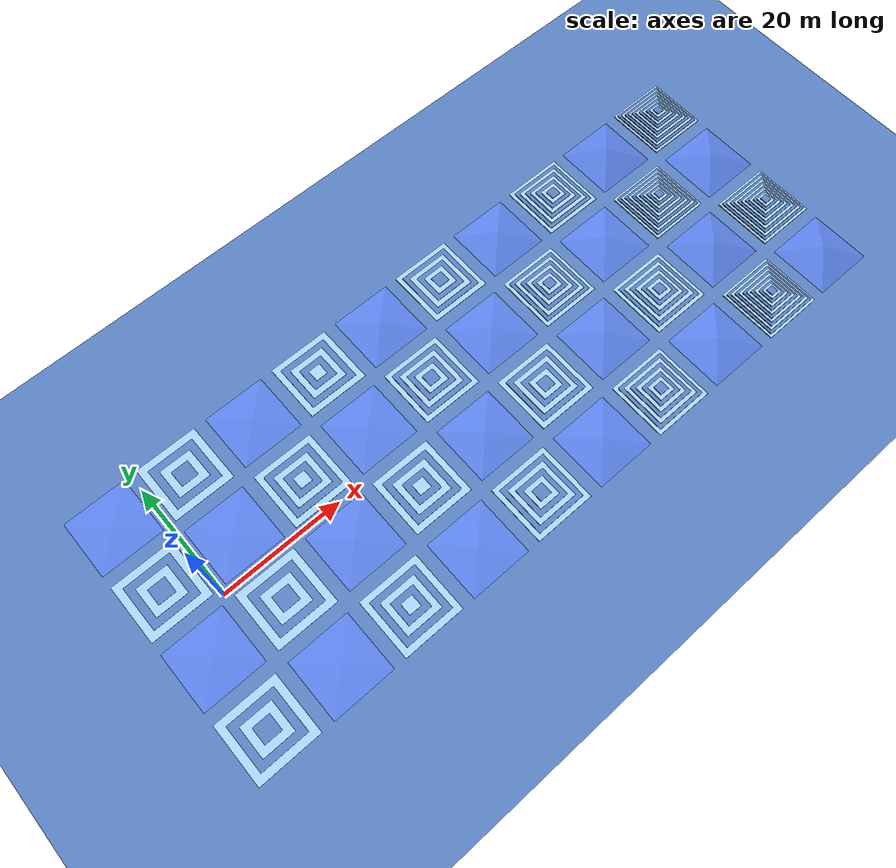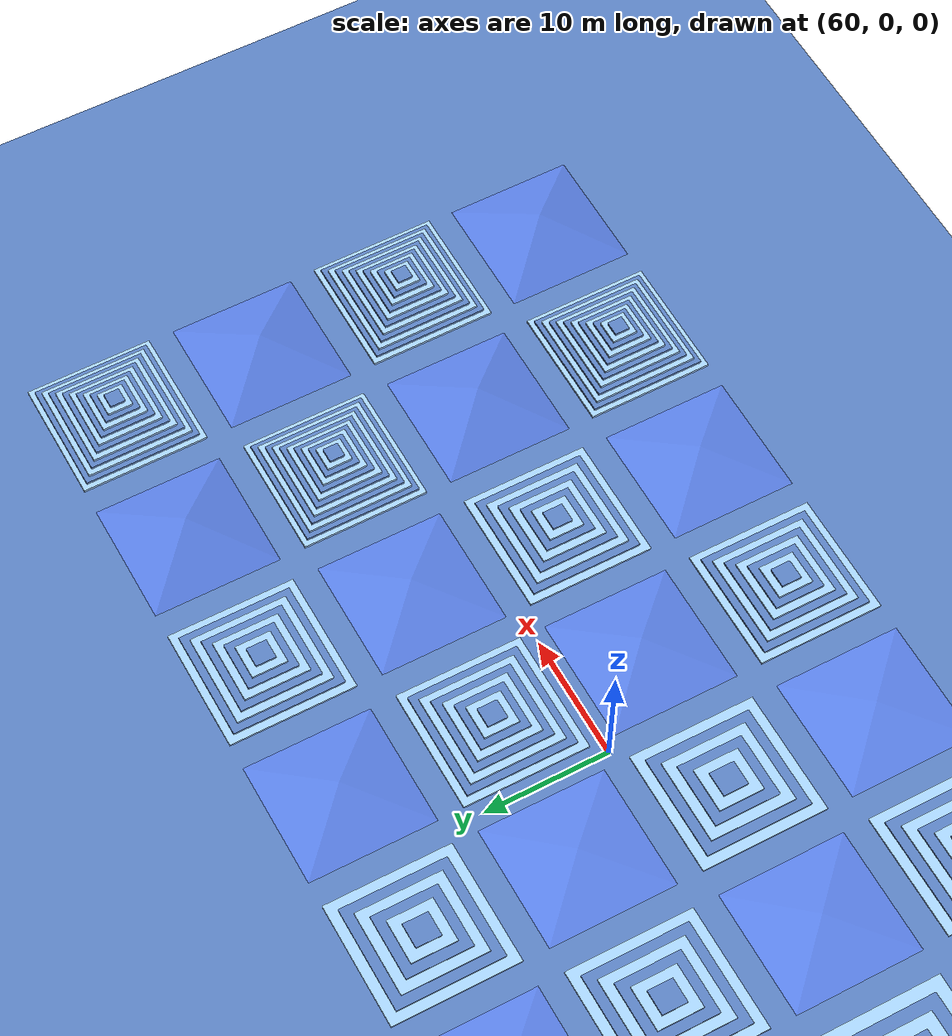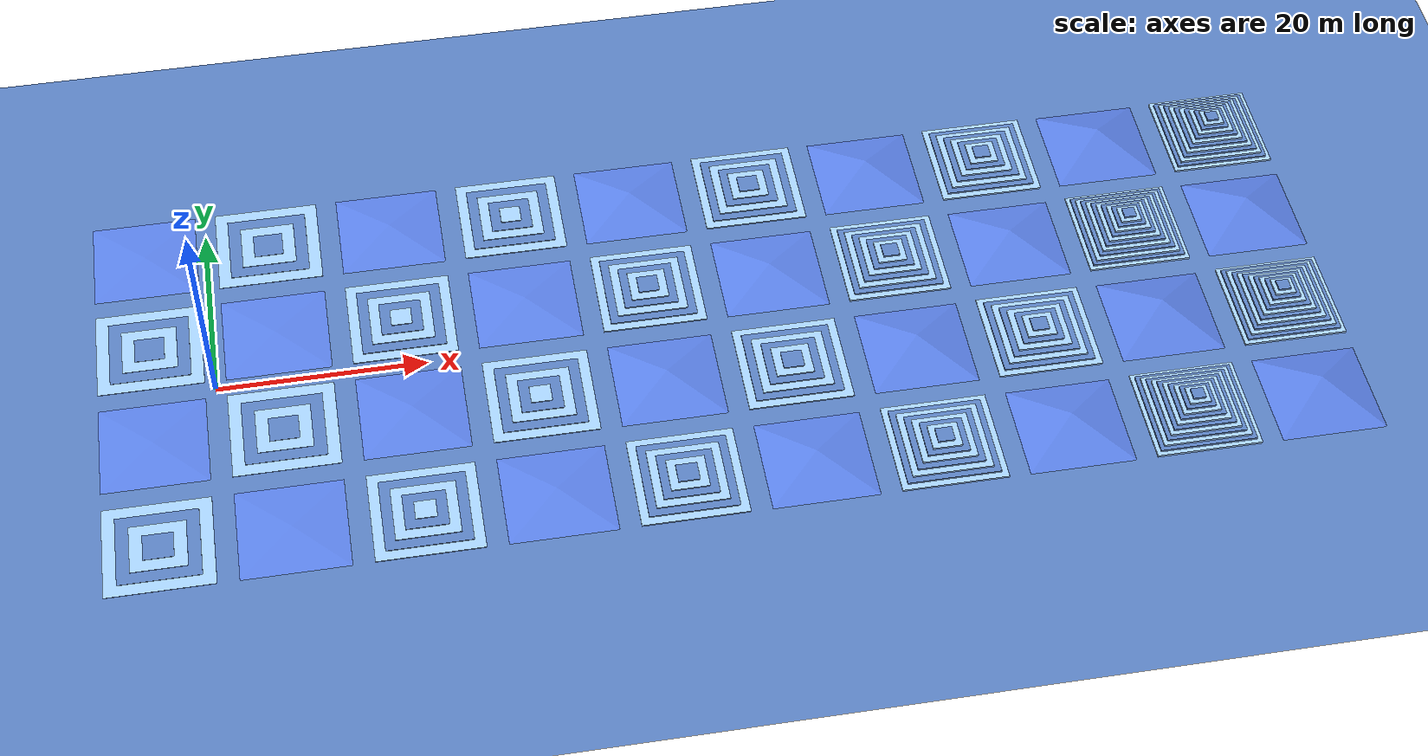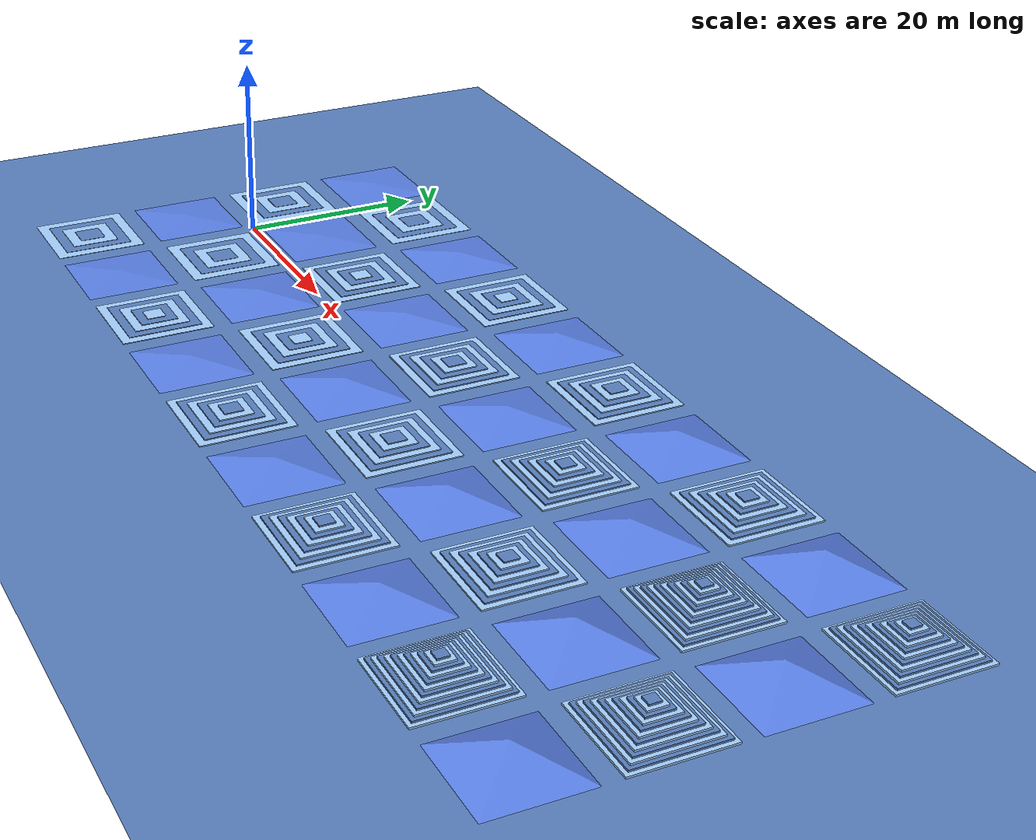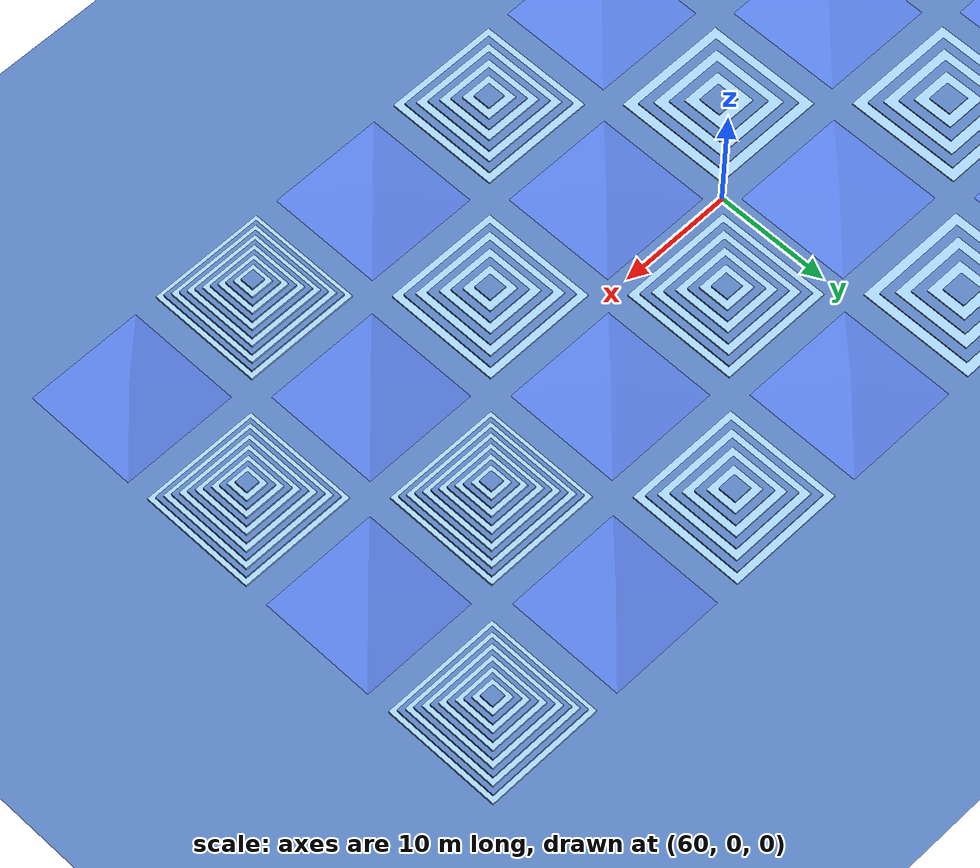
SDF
<?xml version="1.0"?>
<sdf version="1.6">
  <world name="mixed_world">

    <plugin filename="gz-sim-physics-system" name="gz::sim::systems::Physics"/>
    <plugin filename="gz-sim-air-pressure-system" name="gz::sim::systems::AirPressure"/>
    <plugin filename="gz-sim-altimeter-system" name="gz::sim::systems::Altimeter"/>
    <plugin filename="gz-sim-imu-system" name="gz::sim::systems::Imu"/>
    <plugin filename="gz-sim-sensors-system" name="gz::sim::systems::Sensors">
      <render_engine>ogre2</render_engine>
    </plugin>
    <plugin filename="gz-sim-magnetometer-system" name="gz::sim::systems::Magnetometer"/>
    <plugin filename="gz-sim-forcetorque-system" name="gz::sim::systems::ForceTorque"/>
    <plugin filename="gz-sim-user-commands-system" name="gz::sim::systems::UserCommands"/>
    <plugin filename="gz-sim-scene-broadcaster-system" name="gz::sim::systems::SceneBroadcaster"/>

    <gravity>0 0 -9.81</gravity>

    <light type="directional" name="sun">
      <cast_shadows>true</cast_shadows>
      <pose>0 0 10 0 0 0</pose>
      <diffuse>0.8 0.8 0.8 1</diffuse>
      <specular>0.2 0.2 0.2 1</specular>
      <attenuation>
        <range>1000</range>
        <constant>0.9</constant>
        <linear>0.01</linear>
        <quadratic>0.001</quadratic>
      </attenuation>
      <direction>-0.5 0.1 -0.9</direction>
    </light>

    <physics name="update_rate" type="ode">
      <real_time_update_rate>1000</real_time_update_rate>
      <max_step_size>0.001</max_step_size>
      <max_contacts>10</max_contacts>
      <ode>
        <solver>
          <iters>50</iters>
          <sor>1.20</sor>
        </solver>
        <constraints>
          <contact_surface_layer>0.0002</contact_surface_layer>
          <contact_max_correcting_vel>500</contact_max_correcting_vel>
          <cfm>0.000001</cfm>
          <erp>0.3</erp>
        </constraints>
      </ode>
    </physics>

    <model name="ground_plane">
      <static>true</static>
      <link name="link">
        <collision name="collision">
          <geometry><plane><normal>0 0 1</normal><size>500 500</size></plane></geometry>
          <surface><friction><ode><mu>0.8</mu><mu2>0.8</mu2></ode></friction></surface>
        </collision>
        <visual name="visual">
          <geometry><plane><normal>0 0 1</normal><size>500 500</size></plane></geometry>
          <material><ambient>0.35 0.5 0.75 1</ambient><diffuse>0.35 0.5 0.75 1</diffuse></material>
        </visual>
      </link>
    </model>

    <model name="pyramid_lvl0_stairs_1"><static>true</static><pose>-6 6 0 0 0 0</pose>
      <link name="s1"><pose>0 0 0.02 0 0 0</pose>
        <collision name="c"><geometry><box><size>10 10 0.04</size></box></geometry><surface><friction><ode><mu>0.8</mu><mu2>0.8</mu2></ode></friction></surface></collision>
        <visual name="v"><geometry><box><size>10 10 0.04</size></box></geometry><material><ambient>0.65 0.82 1 1</ambient><diffuse>0.65 0.82 1 1</diffuse></material></visual>
      </link>
      <link name="s2"><pose>0 0 0.06 0 0 0</pose>
        <collision name="c"><geometry><box><size>7.6 7.6 0.04</size></box></geometry><surface><friction><ode><mu>0.8</mu><mu2>0.8</mu2></ode></friction></surface></collision>
        <visual name="v"><geometry><box><size>7.6 7.6 0.04</size></box></geometry><material><ambient>0.35 0.5 0.75 1</ambient><diffuse>0.35 0.5 0.75 1</diffuse></material></visual>
      </link>
      <link name="s3"><pose>0 0 0.10 0 0 0</pose>
        <collision name="c"><geometry><box><size>5.2 5.2 0.04</size></box></geometry><surface><friction><ode><mu>0.8</mu><mu2>0.8</mu2></ode></friction></surface></collision>
        <visual name="v"><geometry><box><size>5.2 5.2 0.04</size></box></geometry><material><ambient>0.65 0.82 1 1</ambient><diffuse>0.65 0.82 1 1</diffuse></material></visual>
      </link>
      <link name="s4"><pose>0 0 0.14 0 0 0</pose>
        <collision name="c"><geometry><box><size>2.8 2.8 0.04</size></box></geometry><surface><friction><ode><mu>0.8</mu><mu2>0.8</mu2></ode></friction></surface></collision>
        <visual name="v"><geometry><box><size>2.8 2.8 0.04</size></box></geometry><material><ambient>0.35 0.5 0.75 1</ambient><diffuse>0.35 0.5 0.75 1</diffuse></material></visual>
      </link>
    </model>

    <model name="pyramid_lvl0_slope_2"><static>true</static><pose>-6 -6 0 0 0 0</pose>
      <link name="slope">
        <collision name="c"><geometry><mesh><uri>model://kyon_urdf/meshes/pyramid_slope_05deg_10x10.stl</uri></mesh></geometry><surface><friction><ode><mu>0.7</mu><mu2>0.7</mu2></ode></friction></surface></collision>
        <visual name="v"><geometry><mesh><uri>model://kyon_urdf/meshes/pyramid_slope_05deg_10x10.stl</uri></mesh></geometry><material><ambient>0.35 0.5 0.9 1</ambient><diffuse>0.35 0.5 0.9 1</diffuse></material></visual>
      </link>
    </model>

    <model name="pyramid_lvl0_stairs_3"><static>true</static><pose>6 -6 0 0 0 0</pose>
      <link name="s1"><pose>0 0 0.02 0 0 0</pose>
        <collision name="c"><geometry><box><size>10 10 0.04</size></box></geometry><surface><friction><ode><mu>0.8</mu><mu2>0.8</mu2></ode></friction></surface></collision>
        <visual name="v"><geometry><box><size>10 10 0.04</size></box></geometry><material><ambient>0.65 0.82 1 1</ambient><diffuse>0.65 0.82 1 1</diffuse></material></visual>
      </link>
      <link name="s2"><pose>0 0 0.06 0 0 0</pose>
        <collision name="c"><geometry><box><size>7.6 7.6 0.04</size></box></geometry><surface><friction><ode><mu>0.8</mu><mu2>0.8</mu2></ode></friction></surface></collision>
        <visual name="v"><geometry><box><size>7.6 7.6 0.04</size></box></geometry><material><ambient>0.35 0.5 0.75 1</ambient><diffuse>0.35 0.5 0.75 1</diffuse></material></visual>
      </link>
      <link name="s3"><pose>0 0 0.10 0 0 0</pose>
        <collision name="c"><geometry><box><size>5.2 5.2 0.04</size></box></geometry><surface><friction><ode><mu>0.8</mu><mu2>0.8</mu2></ode></friction></surface></collision>
        <visual name="v"><geometry><box><size>5.2 5.2 0.04</size></box></geometry><material><ambient>0.65 0.82 1 1</ambient><diffuse>0.65 0.82 1 1</diffuse></material></visual>
      </link>
      <link name="s4"><pose>0 0 0.14 0 0 0</pose>
        <collision name="c"><geometry><box><size>2.8 2.8 0.04</size></box></geometry><surface><friction><ode><mu>0.8</mu><mu2>0.8</mu2></ode></friction></surface></collision>
        <visual name="v"><geometry><box><size>2.8 2.8 0.04</size></box></geometry><material><ambient>0.35 0.5 0.75 1</ambient><diffuse>0.35 0.5 0.75 1</diffuse></material></visual>
      </link>
    </model>

    <model name="pyramid_lvl0_slope_4"><static>true</static><pose>6 6 0 0 0 0</pose>
      <link name="slope">
        <collision name="c"><geometry><mesh><uri>model://kyon_urdf/meshes/pyramid_slope_05deg_10x10.stl</uri></mesh></geometry><surface><friction><ode><mu>0.7</mu><mu2>0.7</mu2></ode></friction></surface></collision>
        <visual name="v"><geometry><mesh><uri>model://kyon_urdf/meshes/pyramid_slope_05deg_10x10.stl</uri></mesh></geometry><material><ambient>0.35 0.5 0.9 1</ambient><diffuse>0.35 0.5 0.9 1</diffuse></material></visual>
      </link>
    </model>

    <model name="pyramid_lvl0_stairs_5"><static>true</static><pose>-6 -18 0 0 0 0</pose>
      <link name="s1"><pose>0 0 0.02 0 0 0</pose>
        <collision name="c"><geometry><box><size>10 10 0.04</size></box></geometry><surface><friction><ode><mu>0.8</mu><mu2>0.8</mu2></ode></friction></surface></collision>
        <visual name="v"><geometry><box><size>10 10 0.04</size></box></geometry><material><ambient>0.65 0.82 1 1</ambient><diffuse>0.65 0.82 1 1</diffuse></material></visual>
      </link>
      <link name="s2"><pose>0 0 0.06 0 0 0</pose>
        <collision name="c"><geometry><box><size>7.6 7.6 0.04</size></box></geometry><surface><friction><ode><mu>0.8</mu><mu2>0.8</mu2></ode></friction></surface></collision>
        <visual name="v"><geometry><box><size>7.6 7.6 0.04</size></box></geometry><material><ambient>0.35 0.5 0.75 1</ambient><diffuse>0.35 0.5 0.75 1</diffuse></material></visual>
      </link>
      <link name="s3"><pose>0 0 0.10 0 0 0</pose>
        <collision name="c"><geometry><box><size>5.2 5.2 0.04</size></box></geometry><surface><friction><ode><mu>0.8</mu><mu2>0.8</mu2></ode></friction></surface></collision>
        <visual name="v"><geometry><box><size>5.2 5.2 0.04</size></box></geometry><material><ambient>0.65 0.82 1 1</ambient><diffuse>0.65 0.82 1 1</diffuse></material></visual>
      </link>
      <link name="s4"><pose>0 0 0.14 0 0 0</pose>
        <collision name="c"><geometry><box><size>2.8 2.8 0.04</size></box></geometry><surface><friction><ode><mu>0.8</mu><mu2>0.8</mu2></ode></friction></surface></collision>
        <visual name="v"><geometry><box><size>2.8 2.8 0.04</size></box></geometry><material><ambient>0.35 0.5 0.75 1</ambient><diffuse>0.35 0.5 0.75 1</diffuse></material></visual>
      </link>
    </model>

    <model name="pyramid_lvl0_slope_6"><static>true</static><pose>6 -18 0 0 0 0</pose>
      <link name="slope">
        <collision name="c"><geometry><mesh><uri>model://kyon_urdf/meshes/pyramid_slope_05deg_10x10.stl</uri></mesh></geometry><surface><friction><ode><mu>0.7</mu><mu2>0.7</mu2></ode></friction></surface></collision>
        <visual name="v"><geometry><mesh><uri>model://kyon_urdf/meshes/pyramid_slope_05deg_10x10.stl</uri></mesh></geometry><material><ambient>0.35 0.5 0.9 1</ambient><diffuse>0.35 0.5 0.9 1</diffuse></material></visual>
      </link>
    </model>

    <model name="pyramid_lvl0_stairs_7"><static>true</static><pose>6 18 0 0 0 0</pose>
      <link name="s1"><pose>0 0 0.02 0 0 0</pose>
        <collision name="c"><geometry><box><size>10 10 0.04</size></box></geometry><surface><friction><ode><mu>0.8</mu><mu2>0.8</mu2></ode></friction></surface></collision>
        <visual name="v"><geometry><box><size>10 10 0.04</size></box></geometry><material><ambient>0.65 0.82 1 1</ambient><diffuse>0.65 0.82 1 1</diffuse></material></visual>
      </link>
      <link name="s2"><pose>0 0 0.06 0 0 0</pose>
        <collision name="c"><geometry><box><size>7.6 7.6 0.04</size></box></geometry><surface><friction><ode><mu>0.8</mu><mu2>0.8</mu2></ode></friction></surface></collision>
        <visual name="v"><geometry><box><size>7.6 7.6 0.04</size></box></geometry><material><ambient>0.35 0.5 0.75 1</ambient><diffuse>0.35 0.5 0.75 1</diffuse></material></visual>
      </link>
      <link name="s3"><pose>0 0 0.10 0 0 0</pose>
        <collision name="c"><geometry><box><size>5.2 5.2 0.04</size></box></geometry><surface><friction><ode><mu>0.8</mu><mu2>0.8</mu2></ode></friction></surface></collision>
        <visual name="v"><geometry><box><size>5.2 5.2 0.04</size></box></geometry><material><ambient>0.65 0.82 1 1</ambient><diffuse>0.65 0.82 1 1</diffuse></material></visual>
      </link>
      <link name="s4"><pose>0 0 0.14 0 0 0</pose>
        <collision name="c"><geometry><box><size>2.8 2.8 0.04</size></box></geometry><surface><friction><ode><mu>0.8</mu><mu2>0.8</mu2></ode></friction></surface></collision>
        <visual name="v"><geometry><box><size>2.8 2.8 0.04</size></box></geometry><material><ambient>0.35 0.5 0.75 1</ambient><diffuse>0.35 0.5 0.75 1</diffuse></material></visual>
      </link>
    </model>

    <model name="pyramid_lvl0_slope_8"><static>true</static><pose>-6 18 0 0 0 0</pose>
      <link name="slope">
        <collision name="c"><geometry><mesh><uri>model://kyon_urdf/meshes/pyramid_slope_05deg_10x10.stl</uri></mesh></geometry><surface><friction><ode><mu>0.7</mu><mu2>0.7</mu2></ode></friction></surface></collision>
        <visual name="v"><geometry><mesh><uri>model://kyon_urdf/meshes/pyramid_slope_05deg_10x10.stl</uri></mesh></geometry><material><ambient>0.35 0.5 0.9 1</ambient><diffuse>0.35 0.5 0.9 1</diffuse></material></visual>
      </link>
    </model>

    <model name="pyramid_lvl1_stairs_1"><static>true</static><pose>18 6 0 0 0 0</pose>
      <link name="s1"><pose>0 0 0.04 0 0 0</pose>
        <collision name="c"><geometry><box><size>10 10 0.08</size></box></geometry><surface><friction><ode><mu>0.8</mu><mu2>0.8</mu2></ode></friction></surface></collision>
        <visual name="v"><geometry><box><size>10 10 0.08</size></box></geometry><material><ambient>0.65 0.82 1 1</ambient><diffuse>0.65 0.82 1 1</diffuse></material></visual>
      </link>
      <link name="s2"><pose>0 0 0.12 0 0 0</pose>
        <collision name="c"><geometry><box><size>8 8 0.08</size></box></geometry><surface><friction><ode><mu>0.8</mu><mu2>0.8</mu2></ode></friction></surface></collision>
        <visual name="v"><geometry><box><size>8 8 0.08</size></box></geometry><material><ambient>0.35 0.5 0.75 1</ambient><diffuse>0.35 0.5 0.75 1</diffuse></material></visual>
      </link>
      <link name="s3"><pose>0 0 0.20 0 0 0</pose>
        <collision name="c"><geometry><box><size>6 6 0.08</size></box></geometry><surface><friction><ode><mu>0.8</mu><mu2>0.8</mu2></ode></friction></surface></collision>
        <visual name="v"><geometry><box><size>6 6 0.08</size></box></geometry><material><ambient>0.65 0.82 1 1</ambient><diffuse>0.65 0.82 1 1</diffuse></material></visual>
      </link>
      <link name="s4"><pose>0 0 0.28 0 0 0</pose>
        <collision name="c"><geometry><box><size>4 4 0.08</size></box></geometry><surface><friction><ode><mu>0.8</mu><mu2>0.8</mu2></ode></friction></surface></collision>
        <visual name="v"><geometry><box><size>4 4 0.08</size></box></geometry><material><ambient>0.35 0.5 0.75 1</ambient><diffuse>0.35 0.5 0.75 1</diffuse></material></visual>
      </link>
      <link name="s5"><pose>0 0 0.36 0 0 0</pose>
        <collision name="c"><geometry><box><size>2 2 0.08</size></box></geometry><surface><friction><ode><mu>0.8</mu><mu2>0.8</mu2></ode></friction></surface></collision>
        <visual name="v"><geometry><box><size>2 2 0.08</size></box></geometry><material><ambient>0.65 0.82 1 1</ambient><diffuse>0.65 0.82 1 1</diffuse></material></visual>
      </link>
    </model>

    <model name="pyramid_lvl1_slope_2"><static>true</static><pose>18 -6 0 0 0 0</pose>
      <link name="slope">
        <collision name="c"><geometry><mesh><uri>model://kyon_urdf/meshes/pyramid_slope_10deg_10x10.stl</uri></mesh></geometry><surface><friction><ode><mu>0.7</mu><mu2>0.7</mu2></ode></friction></surface></collision>
        <visual name="v"><geometry><mesh><uri>model://kyon_urdf/meshes/pyramid_slope_10deg_10x10.stl</uri></mesh></geometry><material><ambient>0.35 0.5 0.9 1</ambient><diffuse>0.35 0.5 0.9 1</diffuse></material></visual>
      </link>
    </model>

    <model name="pyramid_lvl1_stairs_3"><static>true</static><pose>30 -6 0 0 0 0</pose>
      <link name="s1"><pose>0 0 0.04 0 0 0</pose>
        <collision name="c"><geometry><box><size>10 10 0.08</size></box></geometry><surface><friction><ode><mu>0.8</mu><mu2>0.8</mu2></ode></friction></surface></collision>
        <visual name="v"><geometry><box><size>10 10 0.08</size></box></geometry><material><ambient>0.65 0.82 1 1</ambient><diffuse>0.65 0.82 1 1</diffuse></material></visual>
      </link>
      <link name="s2"><pose>0 0 0.12 0 0 0</pose>
        <collision name="c"><geometry><box><size>8 8 0.08</size></box></geometry><surface><friction><ode><mu>0.8</mu><mu2>0.8</mu2></ode></friction></surface></collision>
        <visual name="v"><geometry><box><size>8 8 0.08</size></box></geometry><material><ambient>0.35 0.5 0.75 1</ambient><diffuse>0.35 0.5 0.75 1</diffuse></material></visual>
      </link>
      <link name="s3"><pose>0 0 0.20 0 0 0</pose>
        <collision name="c"><geometry><box><size>6 6 0.08</size></box></geometry><surface><friction><ode><mu>0.8</mu><mu2>0.8</mu2></ode></friction></surface></collision>
        <visual name="v"><geometry><box><size>6 6 0.08</size></box></geometry><material><ambient>0.65 0.82 1 1</ambient><diffuse>0.65 0.82 1 1</diffuse></material></visual>
      </link>
      <link name="s4"><pose>0 0 0.28 0 0 0</pose>
        <collision name="c"><geometry><box><size>4 4 0.08</size></box></geometry><surface><friction><ode><mu>0.8</mu><mu2>0.8</mu2></ode></friction></surface></collision>
        <visual name="v"><geometry><box><size>4 4 0.08</size></box></geometry><material><ambient>0.35 0.5 0.75 1</ambient><diffuse>0.35 0.5 0.75 1</diffuse></material></visual>
      </link>
      <link name="s5"><pose>0 0 0.36 0 0 0</pose>
        <collision name="c"><geometry><box><size>2 2 0.08</size></box></geometry><surface><friction><ode><mu>0.8</mu><mu2>0.8</mu2></ode></friction></surface></collision>
        <visual name="v"><geometry><box><size>2 2 0.08</size></box></geometry><material><ambient>0.65 0.82 1 1</ambient><diffuse>0.65 0.82 1 1</diffuse></material></visual>
      </link>
    </model>

    <model name="pyramid_lvl1_slope_4"><static>true</static><pose>30 6 0 0 0 0</pose>
      <link name="slope">
        <collision name="c"><geometry><mesh><uri>model://kyon_urdf/meshes/pyramid_slope_10deg_10x10.stl</uri></mesh></geometry><surface><friction><ode><mu>0.7</mu><mu2>0.7</mu2></ode></friction></surface></collision>
        <visual name="v"><geometry><mesh><uri>model://kyon_urdf/meshes/pyramid_slope_10deg_10x10.stl</uri></mesh></geometry><material><ambient>0.35 0.5 0.9 1</ambient><diffuse>0.35 0.5 0.9 1</diffuse></material></visual>
      </link>
    </model>

    <model name="pyramid_lvl1_slope_5"><static>true</static><pose>18 18 0 0 0 0</pose>
      <link name="slope">
        <collision name="c"><geometry><mesh><uri>model://kyon_urdf/meshes/pyramid_slope_10deg_10x10.stl</uri></mesh></geometry><surface><friction><ode><mu>0.7</mu><mu2>0.7</mu2></ode></friction></surface></collision>
        <visual name="v"><geometry><mesh><uri>model://kyon_urdf/meshes/pyramid_slope_10deg_10x10.stl</uri></mesh></geometry><material><ambient>0.35 0.5 0.9 1</ambient><diffuse>0.35 0.5 0.9 1</diffuse></material></visual>
      </link>
    </model>

    <model name="pyramid_lvl1_stairs_6"><static>true</static><pose>30 18 0 0 0 0</pose>
      <link name="s1"><pose>0 0 0.04 0 0 0</pose>
        <collision name="c"><geometry><box><size>10 10 0.08</size></box></geometry><surface><friction><ode><mu>0.8</mu><mu2>0.8</mu2></ode></friction></surface></collision>
        <visual name="v"><geometry><box><size>10 10 0.08</size></box></geometry><material><ambient>0.65 0.82 1 1</ambient><diffuse>0.65 0.82 1 1</diffuse></material></visual>
      </link>
      <link name="s2"><pose>0 0 0.12 0 0 0</pose>
        <collision name="c"><geometry><box><size>8 8 0.08</size></box></geometry><surface><friction><ode><mu>0.8</mu><mu2>0.8</mu2></ode></friction></surface></collision>
        <visual name="v"><geometry><box><size>8 8 0.08</size></box></geometry><material><ambient>0.35 0.5 0.75 1</ambient><diffuse>0.35 0.5 0.75 1</diffuse></material></visual>
      </link>
      <link name="s3"><pose>0 0 0.20 0 0 0</pose>
        <collision name="c"><geometry><box><size>6 6 0.08</size></box></geometry><surface><friction><ode><mu>0.8</mu><mu2>0.8</mu2></ode></friction></surface></collision>
        <visual name="v"><geometry><box><size>6 6 0.08</size></box></geometry><material><ambient>0.65 0.82 1 1</ambient><diffuse>0.65 0.82 1 1</diffuse></material></visual>
      </link>
      <link name="s4"><pose>0 0 0.28 0 0 0</pose>
        <collision name="c"><geometry><box><size>4 4 0.08</size></box></geometry><surface><friction><ode><mu>0.8</mu><mu2>0.8</mu2></ode></friction></surface></collision>
        <visual name="v"><geometry><box><size>4 4 0.08</size></box></geometry><material><ambient>0.35 0.5 0.75 1</ambient><diffuse>0.35 0.5 0.75 1</diffuse></material></visual>
      </link>
      <link name="s5"><pose>0 0 0.36 0 0 0</pose>
        <collision name="c"><geometry><box><size>2 2 0.08</size></box></geometry><surface><friction><ode><mu>0.8</mu><mu2>0.8</mu2></ode></friction></surface></collision>
        <visual name="v"><geometry><box><size>2 2 0.08</size></box></geometry><material><ambient>0.65 0.82 1 1</ambient><diffuse>0.65 0.82 1 1</diffuse></material></visual>
      </link>
    </model>

    <model name="pyramid_lvl1_stairs_7"><static>true</static><pose>18 -18 0 0 0 0</pose>
      <link name="s1"><pose>0 0 0.04 0 0 0</pose>
        <collision name="c"><geometry><box><size>10 10 0.08</size></box></geometry><surface><friction><ode><mu>0.8</mu><mu2>0.8</mu2></ode></friction></surface></collision>
        <visual name="v"><geometry><box><size>10 10 0.08</size></box></geometry><material><ambient>0.65 0.82 1 1</ambient><diffuse>0.65 0.82 1 1</diffuse></material></visual>
      </link>
      <link name="s2"><pose>0 0 0.12 0 0 0</pose>
        <collision name="c"><geometry><box><size>8 8 0.08</size></box></geometry><surface><friction><ode><mu>0.8</mu><mu2>0.8</mu2></ode></friction></surface></collision>
        <visual name="v"><geometry><box><size>8 8 0.08</size></box></geometry><material><ambient>0.35 0.5 0.75 1</ambient><diffuse>0.35 0.5 0.75 1</diffuse></material></visual>
      </link>
      <link name="s3"><pose>0 0 0.20 0 0 0</pose>
        <collision name="c"><geometry><box><size>6 6 0.08</size></box></geometry><surface><friction><ode><mu>0.8</mu><mu2>0.8</mu2></ode></friction></surface></collision>
        <visual name="v"><geometry><box><size>6 6 0.08</size></box></geometry><material><ambient>0.65 0.82 1 1</ambient><diffuse>0.65 0.82 1 1</diffuse></material></visual>
      </link>
      <link name="s4"><pose>0 0 0.28 0 0 0</pose>
        <collision name="c"><geometry><box><size>4 4 0.08</size></box></geometry><surface><friction><ode><mu>0.8</mu><mu2>0.8</mu2></ode></friction></surface></collision>
        <visual name="v"><geometry><box><size>4 4 0.08</size></box></geometry><material><ambient>0.35 0.5 0.75 1</ambient><diffuse>0.35 0.5 0.75 1</diffuse></material></visual>
      </link>
      <link name="s5"><pose>0 0 0.36 0 0 0</pose>
        <collision name="c"><geometry><box><size>2 2 0.08</size></box></geometry><surface><friction><ode><mu>0.8</mu><mu2>0.8</mu2></ode></friction></surface></collision>
        <visual name="v"><geometry><box><size>2 2 0.08</size></box></geometry><material><ambient>0.65 0.82 1 1</ambient><diffuse>0.65 0.82 1 1</diffuse></material></visual>
      </link>
    </model>

    <model name="pyramid_lvl1_slope_8"><static>true</static><pose>30 -18 0 0 0 0</pose>
      <link name="slope">
        <collision name="c"><geometry><mesh><uri>model://kyon_urdf/meshes/pyramid_slope_10deg_10x10.stl</uri></mesh></geometry><surface><friction><ode><mu>0.7</mu><mu2>0.7</mu2></ode></friction></surface></collision>
        <visual name="v"><geometry><mesh><uri>model://kyon_urdf/meshes/pyramid_slope_10deg_10x10.stl</uri></mesh></geometry><material><ambient>0.35 0.5 0.9 1</ambient><diffuse>0.35 0.5 0.9 1</diffuse></material></visual>
      </link>
    </model>

    <model name="pyramid_lvl2_slope_1"><static>true</static><pose>42 -6 0 0 0 0</pose>
      <link name="slope">
        <collision name="c"><geometry><mesh><uri>model://kyon_urdf/meshes/pyramid_slope_15deg_10x10.stl</uri></mesh></geometry><surface><friction><ode><mu>0.7</mu><mu2>0.7</mu2></ode></friction></surface></collision>
        <visual name="v"><geometry><mesh><uri>model://kyon_urdf/meshes/pyramid_slope_15deg_10x10.stl</uri></mesh></geometry><material><ambient>0.35 0.5 0.9 1</ambient><diffuse>0.35 0.5 0.9 1</diffuse></material></visual>
      </link>
    </model>

    <model name="pyramid_lvl2_stairs_2"><static>true</static><pose>42 6 0 0 0 0</pose>
      <link name="s1"><pose>0 0 0.06 0 0 0</pose>
        <collision name="c"><geometry><box><size>10 10 0.12</size></box></geometry><surface><friction><ode><mu>0.8</mu><mu2>0.8</mu2></ode></friction></surface></collision>
        <visual name="v"><geometry><box><size>10 10 0.12</size></box></geometry><material><ambient>0.65 0.82 1 1</ambient><diffuse>0.65 0.82 1 1</diffuse></material></visual>
      </link>
      <link name="s2"><pose>0 0 0.18 0 0 0</pose>
        <collision name="c"><geometry><box><size>8.4 8.4 0.12</size></box></geometry><surface><friction><ode><mu>0.8</mu><mu2>0.8</mu2></ode></friction></surface></collision>
        <visual name="v"><geometry><box><size>8.4 8.4 0.12</size></box></geometry><material><ambient>0.35 0.5 0.75 1</ambient><diffuse>0.35 0.5 0.75 1</diffuse></material></visual>
      </link>
      <link name="s3"><pose>0 0 0.30 0 0 0</pose>
        <collision name="c"><geometry><box><size>6.8 6.8 0.12</size></box></geometry><surface><friction><ode><mu>0.8</mu><mu2>0.8</mu2></ode></friction></surface></collision>
        <visual name="v"><geometry><box><size>6.8 6.8 0.12</size></box></geometry><material><ambient>0.65 0.82 1 1</ambient><diffuse>0.65 0.82 1 1</diffuse></material></visual>
      </link>
      <link name="s4"><pose>0 0 0.42 0 0 0</pose>
        <collision name="c"><geometry><box><size>5.2 5.2 0.12</size></box></geometry><surface><friction><ode><mu>0.8</mu><mu2>0.8</mu2></ode></friction></surface></collision>
        <visual name="v"><geometry><box><size>5.2 5.2 0.12</size></box></geometry><material><ambient>0.35 0.5 0.75 1</ambient><diffuse>0.35 0.5 0.75 1</diffuse></material></visual>
      </link>
      <link name="s5"><pose>0 0 0.54 0 0 0</pose>
        <collision name="c"><geometry><box><size>3.6 3.6 0.12</size></box></geometry><surface><friction><ode><mu>0.8</mu><mu2>0.8</mu2></ode></friction></surface></collision>
        <visual name="v"><geometry><box><size>3.6 3.6 0.12</size></box></geometry><material><ambient>0.65 0.82 1 1</ambient><diffuse>0.65 0.82 1 1</diffuse></material></visual>
      </link>
      <link name="s6"><pose>0 0 0.66 0 0 0</pose>
        <collision name="c"><geometry><box><size>2 2 0.12</size></box></geometry><surface><friction><ode><mu>0.8</mu><mu2>0.8</mu2></ode></friction></surface></collision>
        <visual name="v"><geometry><box><size>2 2 0.12</size></box></geometry><material><ambient>0.35 0.5 0.75 1</ambient><diffuse>0.35 0.5 0.75 1</diffuse></material></visual>
      </link>
    </model>

    <model name="pyramid_lvl2_stairs_3"><static>true</static><pose>54 -6 0 0 0 0</pose>
      <link name="s1"><pose>0 0 0.06 0 0 0</pose>
        <collision name="c"><geometry><box><size>10 10 0.12</size></box></geometry><surface><friction><ode><mu>0.8</mu><mu2>0.8</mu2></ode></friction></surface></collision>
        <visual name="v"><geometry><box><size>10 10 0.12</size></box></geometry><material><ambient>0.65 0.82 1 1</ambient><diffuse>0.65 0.82 1 1</diffuse></material></visual>
      </link>
      <link name="s2"><pose>0 0 0.18 0 0 0</pose>
        <collision name="c"><geometry><box><size>8.4 8.4 0.12</size></box></geometry><surface><friction><ode><mu>0.8</mu><mu2>0.8</mu2></ode></friction></surface></collision>
        <visual name="v"><geometry><box><size>8.4 8.4 0.12</size></box></geometry><material><ambient>0.35 0.5 0.75 1</ambient><diffuse>0.35 0.5 0.75 1</diffuse></material></visual>
      </link>
      <link name="s3"><pose>0 0 0.30 0 0 0</pose>
        <collision name="c"><geometry><box><size>6.8 6.8 0.12</size></box></geometry><surface><friction><ode><mu>0.8</mu><mu2>0.8</mu2></ode></friction></surface></collision>
        <visual name="v"><geometry><box><size>6.8 6.8 0.12</size></box></geometry><material><ambient>0.65 0.82 1 1</ambient><diffuse>0.65 0.82 1 1</diffuse></material></visual>
      </link>
      <link name="s4"><pose>0 0 0.42 0 0 0</pose>
        <collision name="c"><geometry><box><size>5.2 5.2 0.12</size></box></geometry><surface><friction><ode><mu>0.8</mu><mu2>0.8</mu2></ode></friction></surface></collision>
        <visual name="v"><geometry><box><size>5.2 5.2 0.12</size></box></geometry><material><ambient>0.35 0.5 0.75 1</ambient><diffuse>0.35 0.5 0.75 1</diffuse></material></visual>
      </link>
      <link name="s5"><pose>0 0 0.54 0 0 0</pose>
        <collision name="c"><geometry><box><size>3.6 3.6 0.12</size></box></geometry><surface><friction><ode><mu>0.8</mu><mu2>0.8</mu2></ode></friction></surface></collision>
        <visual name="v"><geometry><box><size>3.6 3.6 0.12</size></box></geometry><material><ambient>0.65 0.82 1 1</ambient><diffuse>0.65 0.82 1 1</diffuse></material></visual>
      </link>
      <link name="s6"><pose>0 0 0.66 0 0 0</pose>
        <collision name="c"><geometry><box><size>2 2 0.12</size></box></geometry><surface><friction><ode><mu>0.8</mu><mu2>0.8</mu2></ode></friction></surface></collision>
        <visual name="v"><geometry><box><size>2 2 0.12</size></box></geometry><material><ambient>0.35 0.5 0.75 1</ambient><diffuse>0.35 0.5 0.75 1</diffuse></material></visual>
      </link>
    </model>

    <model name="pyramid_lvl2_slope_4"><static>true</static><pose>54 6 0 0 0 0</pose>
      <link name="slope">
        <collision name="c"><geometry><mesh><uri>model://kyon_urdf/meshes/pyramid_slope_15deg_10x10.stl</uri></mesh></geometry><surface><friction><ode><mu>0.7</mu><mu2>0.7</mu2></ode></friction></surface></collision>
        <visual name="v"><geometry><mesh><uri>model://kyon_urdf/meshes/pyramid_slope_15deg_10x10.stl</uri></mesh></geometry><material><ambient>0.35 0.5 0.9 1</ambient><diffuse>0.35 0.5 0.9 1</diffuse></material></visual>
      </link>
    </model>

    <model name="pyramid_lvl2_slope_5"><static>true</static><pose>42 18 0 0 0 0</pose>
      <link name="slope">
        <collision name="c"><geometry><mesh><uri>model://kyon_urdf/meshes/pyramid_slope_15deg_10x10.stl</uri></mesh></geometry><surface><friction><ode><mu>0.7</mu><mu2>0.7</mu2></ode></friction></surface></collision>
        <visual name="v"><geometry><mesh><uri>model://kyon_urdf/meshes/pyramid_slope_15deg_10x10.stl</uri></mesh></geometry><material><ambient>0.35 0.5 0.9 1</ambient><diffuse>0.35 0.5 0.9 1</diffuse></material></visual>
      </link>
    </model>

    <model name="pyramid_lvl2_stairs_6"><static>true</static><pose>54 18 0 0 0 0</pose>
      <link name="s1"><pose>0 0 0.06 0 0 0</pose>
        <collision name="c"><geometry><box><size>10 10 0.12</size></box></geometry><surface><friction><ode><mu>0.8</mu><mu2>0.8</mu2></ode></friction></surface></collision>
        <visual name="v"><geometry><box><size>10 10 0.12</size></box></geometry><material><ambient>0.65 0.82 1 1</ambient><diffuse>0.65 0.82 1 1</diffuse></material></visual>
      </link>
      <link name="s2"><pose>0 0 0.18 0 0 0</pose>
        <collision name="c"><geometry><box><size>8.4 8.4 0.12</size></box></geometry><surface><friction><ode><mu>0.8</mu><mu2>0.8</mu2></ode></friction></surface></collision>
        <visual name="v"><geometry><box><size>8.4 8.4 0.12</size></box></geometry><material><ambient>0.35 0.5 0.75 1</ambient><diffuse>0.35 0.5 0.75 1</diffuse></material></visual>
      </link>
      <link name="s3"><pose>0 0 0.30 0 0 0</pose>
        <collision name="c"><geometry><box><size>6.8 6.8 0.12</size></box></geometry><surface><friction><ode><mu>0.8</mu><mu2>0.8</mu2></ode></friction></surface></collision>
        <visual name="v"><geometry><box><size>6.8 6.8 0.12</size></box></geometry><material><ambient>0.65 0.82 1 1</ambient><diffuse>0.65 0.82 1 1</diffuse></material></visual>
      </link>
      <link name="s4"><pose>0 0 0.42 0 0 0</pose>
        <collision name="c"><geometry><box><size>5.2 5.2 0.12</size></box></geometry><surface><friction><ode><mu>0.8</mu><mu2>0.8</mu2></ode></friction></surface></collision>
        <visual name="v"><geometry><box><size>5.2 5.2 0.12</size></box></geometry><material><ambient>0.35 0.5 0.75 1</ambient><diffuse>0.35 0.5 0.75 1</diffuse></material></visual>
      </link>
      <link name="s5"><pose>0 0 0.54 0 0 0</pose>
        <collision name="c"><geometry><box><size>3.6 3.6 0.12</size></box></geometry><surface><friction><ode><mu>0.8</mu><mu2>0.8</mu2></ode></friction></surface></collision>
        <visual name="v"><geometry><box><size>3.6 3.6 0.12</size></box></geometry><material><ambient>0.65 0.82 1 1</ambient><diffuse>0.65 0.82 1 1</diffuse></material></visual>
      </link>
      <link name="s6"><pose>0 0 0.66 0 0 0</pose>
        <collision name="c"><geometry><box><size>2 2 0.12</size></box></geometry><surface><friction><ode><mu>0.8</mu><mu2>0.8</mu2></ode></friction></surface></collision>
        <visual name="v"><geometry><box><size>2 2 0.12</size></box></geometry><material><ambient>0.35 0.5 0.75 1</ambient><diffuse>0.35 0.5 0.75 1</diffuse></material></visual>
      </link>
    </model>

    <model name="pyramid_lvl2_stairs_7"><static>true</static><pose>42 -18 0 0 0 0</pose>
      <link name="s1"><pose>0 0 0.06 0 0 0</pose>
        <collision name="c"><geometry><box><size>10 10 0.12</size></box></geometry><surface><friction><ode><mu>0.8</mu><mu2>0.8</mu2></ode></friction></surface></collision>
        <visual name="v"><geometry><box><size>10 10 0.12</size></box></geometry><material><ambient>0.65 0.82 1 1</ambient><diffuse>0.65 0.82 1 1</diffuse></material></visual>
      </link>
      <link name="s2"><pose>0 0 0.18 0 0 0</pose>
        <collision name="c"><geometry><box><size>8.4 8.4 0.12</size></box></geometry><surface><friction><ode><mu>0.8</mu><mu2>0.8</mu2></ode></friction></surface></collision>
        <visual name="v"><geometry><box><size>8.4 8.4 0.12</size></box></geometry><material><ambient>0.35 0.5 0.75 1</ambient><diffuse>0.35 0.5 0.75 1</diffuse></material></visual>
      </link>
      <link name="s3"><pose>0 0 0.30 0 0 0</pose>
        <collision name="c"><geometry><box><size>6.8 6.8 0.12</size></box></geometry><surface><friction><ode><mu>0.8</mu><mu2>0.8</mu2></ode></friction></surface></collision>
        <visual name="v"><geometry><box><size>6.8 6.8 0.12</size></box></geometry><material><ambient>0.65 0.82 1 1</ambient><diffuse>0.65 0.82 1 1</diffuse></material></visual>
      </link>
      <link name="s4"><pose>0 0 0.42 0 0 0</pose>
        <collision name="c"><geometry><box><size>5.2 5.2 0.12</size></box></geometry><surface><friction><ode><mu>0.8</mu><mu2>0.8</mu2></ode></friction></surface></collision>
        <visual name="v"><geometry><box><size>5.2 5.2 0.12</size></box></geometry><material><ambient>0.35 0.5 0.75 1</ambient><diffuse>0.35 0.5 0.75 1</diffuse></material></visual>
      </link>
      <link name="s5"><pose>0 0 0.54 0 0 0</pose>
        <collision name="c"><geometry><box><size>3.6 3.6 0.12</size></box></geometry><surface><friction><ode><mu>0.8</mu><mu2>0.8</mu2></ode></friction></surface></collision>
        <visual name="v"><geometry><box><size>3.6 3.6 0.12</size></box></geometry><material><ambient>0.65 0.82 1 1</ambient><diffuse>0.65 0.82 1 1</diffuse></material></visual>
      </link>
      <link name="s6"><pose>0 0 0.66 0 0 0</pose>
        <collision name="c"><geometry><box><size>2 2 0.12</size></box></geometry><surface><friction><ode><mu>0.8</mu><mu2>0.8</mu2></ode></friction></surface></collision>
        <visual name="v"><geometry><box><size>2 2 0.12</size></box></geometry><material><ambient>0.35 0.5 0.75 1</ambient><diffuse>0.35 0.5 0.75 1</diffuse></material></visual>
      </link>
    </model>

    <model name="pyramid_lvl2_slope_8"><static>true</static><pose>54 -18 0 0 0 0</pose>
      <link name="slope">
        <collision name="c"><geometry><mesh><uri>model://kyon_urdf/meshes/pyramid_slope_15deg_10x10.stl</uri></mesh></geometry><surface><friction><ode><mu>0.7</mu><mu2>0.7</mu2></ode></friction></surface></collision>
        <visual name="v"><geometry><mesh><uri>model://kyon_urdf/meshes/pyramid_slope_15deg_10x10.stl</uri></mesh></geometry><material><ambient>0.35 0.5 0.9 1</ambient><diffuse>0.35 0.5 0.9 1</diffuse></material></visual>
      </link>
    </model>

    <model name="pyramid_lvl3_stairs_1"><static>true</static><pose>66 6 0 0 0 0</pose>
      <link name="s1"><pose>0 0 0.08 0 0 0</pose>
        <collision name="c"><geometry><box><size>10 10 0.16</size></box></geometry><surface><friction><ode><mu>0.8</mu><mu2>0.8</mu2></ode></friction></surface></collision>
        <visual name="v"><geometry><box><size>10 10 0.16</size></box></geometry><material><ambient>0.65 0.82 1 1</ambient><diffuse>0.65 0.82 1 1</diffuse></material></visual>
      </link>
      <link name="s2"><pose>0 0 0.24 0 0 0</pose>
        <collision name="c"><geometry><box><size>8.8 8.8 0.16</size></box></geometry><surface><friction><ode><mu>0.8</mu><mu2>0.8</mu2></ode></friction></surface></collision>
        <visual name="v"><geometry><box><size>8.8 8.8 0.16</size></box></geometry><material><ambient>0.35 0.5 0.75 1</ambient><diffuse>0.35 0.5 0.75 1</diffuse></material></visual>
      </link>
      <link name="s3"><pose>0 0 0.40 0 0 0</pose>
        <collision name="c"><geometry><box><size>7.6 7.6 0.16</size></box></geometry><surface><friction><ode><mu>0.8</mu><mu2>0.8</mu2></ode></friction></surface></collision>
        <visual name="v"><geometry><box><size>7.6 7.6 0.16</size></box></geometry><material><ambient>0.65 0.82 1 1</ambient><diffuse>0.65 0.82 1 1</diffuse></material></visual>
      </link>
      <link name="s4"><pose>0 0 0.56 0 0 0</pose>
        <collision name="c"><geometry><box><size>6.4 6.4 0.16</size></box></geometry><surface><friction><ode><mu>0.8</mu><mu2>0.8</mu2></ode></friction></surface></collision>
        <visual name="v"><geometry><box><size>6.4 6.4 0.16</size></box></geometry><material><ambient>0.35 0.5 0.75 1</ambient><diffuse>0.35 0.5 0.75 1</diffuse></material></visual>
      </link>
      <link name="s5"><pose>0 0 0.72 0 0 0</pose>
        <collision name="c"><geometry><box><size>5.2 5.2 0.16</size></box></geometry><surface><friction><ode><mu>0.8</mu><mu2>0.8</mu2></ode></friction></surface></collision>
        <visual name="v"><geometry><box><size>5.2 5.2 0.16</size></box></geometry><material><ambient>0.65 0.82 1 1</ambient><diffuse>0.65 0.82 1 1</diffuse></material></visual>
      </link>
      <link name="s6"><pose>0 0 0.88 0 0 0</pose>
        <collision name="c"><geometry><box><size>4 4 0.16</size></box></geometry><surface><friction><ode><mu>0.8</mu><mu2>0.8</mu2></ode></friction></surface></collision>
        <visual name="v"><geometry><box><size>4 4 0.16</size></box></geometry><material><ambient>0.35 0.5 0.75 1</ambient><diffuse>0.35 0.5 0.75 1</diffuse></material></visual>
      </link>
      <link name="s7"><pose>0 0 1.04 0 0 0</pose>
        <collision name="c"><geometry><box><size>2.8 2.8 0.16</size></box></geometry><surface><friction><ode><mu>0.8</mu><mu2>0.8</mu2></ode></friction></surface></collision>
        <visual name="v"><geometry><box><size>2.8 2.8 0.16</size></box></geometry><material><ambient>0.65 0.82 1 1</ambient><diffuse>0.65 0.82 1 1</diffuse></material></visual>
      </link>
      <link name="s8"><pose>0 0 1.20 0 0 0</pose>
        <collision name="c"><geometry><box><size>1.6 1.6 0.16</size></box></geometry><surface><friction><ode><mu>0.8</mu><mu2>0.8</mu2></ode></friction></surface></collision>
        <visual name="v"><geometry><box><size>1.6 1.6 0.16</size></box></geometry><material><ambient>0.35 0.5 0.75 1</ambient><diffuse>0.35 0.5 0.75 1</diffuse></material></visual>
      </link>
    </model>

    <model name="pyramid_lvl3_slope_2"><static>true</static><pose>66 -6 0 0 0 0</pose>
      <link name="slope">
        <collision name="c"><geometry><mesh><uri>model://kyon_urdf/meshes/pyramid_slope_20deg_10x10.stl</uri></mesh></geometry><surface><friction><ode><mu>0.7</mu><mu2>0.7</mu2></ode></friction></surface></collision>
        <visual name="v"><geometry><mesh><uri>model://kyon_urdf/meshes/pyramid_slope_20deg_10x10.stl</uri></mesh></geometry><material><ambient>0.35 0.5 0.9 1</ambient><diffuse>0.35 0.5 0.9 1</diffuse></material></visual>
      </link>
    </model>

    <model name="pyramid_lvl3_slope_3"><static>true</static><pose>78 6 0 0 0 0</pose>
      <link name="slope">
        <collision name="c"><geometry><mesh><uri>model://kyon_urdf/meshes/pyramid_slope_20deg_10x10.stl</uri></mesh></geometry><surface><friction><ode><mu>0.7</mu><mu2>0.7</mu2></ode></friction></surface></collision>
        <visual name="v"><geometry><mesh><uri>model://kyon_urdf/meshes/pyramid_slope_20deg_10x10.stl</uri></mesh></geometry><material><ambient>0.35 0.5 0.9 1</ambient><diffuse>0.35 0.5 0.9 1</diffuse></material></visual>
      </link>
    </model>

    <model name="pyramid_lvl3_stairs_4"><static>true</static><pose>78 -6 0 0 0 0</pose>
      <link name="s1"><pose>0 0 0.08 0 0 0</pose>
        <collision name="c"><geometry><box><size>10 10 0.16</size></box></geometry><surface><friction><ode><mu>0.8</mu><mu2>0.8</mu2></ode></friction></surface></collision>
        <visual name="v"><geometry><box><size>10 10 0.16</size></box></geometry><material><ambient>0.65 0.82 1 1</ambient><diffuse>0.65 0.82 1 1</diffuse></material></visual>
      </link>
      <link name="s2"><pose>0 0 0.24 0 0 0</pose>
        <collision name="c"><geometry><box><size>8.8 8.8 0.16</size></box></geometry><surface><friction><ode><mu>0.8</mu><mu2>0.8</mu2></ode></friction></surface></collision>
        <visual name="v"><geometry><box><size>8.8 8.8 0.16</size></box></geometry><material><ambient>0.35 0.5 0.75 1</ambient><diffuse>0.35 0.5 0.75 1</diffuse></material></visual>
      </link>
      <link name="s3"><pose>0 0 0.40 0 0 0</pose>
        <collision name="c"><geometry><box><size>7.6 7.6 0.16</size></box></geometry><surface><friction><ode><mu>0.8</mu><mu2>0.8</mu2></ode></friction></surface></collision>
        <visual name="v"><geometry><box><size>7.6 7.6 0.16</size></box></geometry><material><ambient>0.65 0.82 1 1</ambient><diffuse>0.65 0.82 1 1</diffuse></material></visual>
      </link>
      <link name="s4"><pose>0 0 0.56 0 0 0</pose>
        <collision name="c"><geometry><box><size>6.4 6.4 0.16</size></box></geometry><surface><friction><ode><mu>0.8</mu><mu2>0.8</mu2></ode></friction></surface></collision>
        <visual name="v"><geometry><box><size>6.4 6.4 0.16</size></box></geometry><material><ambient>0.35 0.5 0.75 1</ambient><diffuse>0.35 0.5 0.75 1</diffuse></material></visual>
      </link>
      <link name="s5"><pose>0 0 0.72 0 0 0</pose>
        <collision name="c"><geometry><box><size>5.2 5.2 0.16</size></box></geometry><surface><friction><ode><mu>0.8</mu><mu2>0.8</mu2></ode></friction></surface></collision>
        <visual name="v"><geometry><box><size>5.2 5.2 0.16</size></box></geometry><material><ambient>0.65 0.82 1 1</ambient><diffuse>0.65 0.82 1 1</diffuse></material></visual>
      </link>
      <link name="s6"><pose>0 0 0.88 0 0 0</pose>
        <collision name="c"><geometry><box><size>4 4 0.16</size></box></geometry><surface><friction><ode><mu>0.8</mu><mu2>0.8</mu2></ode></friction></surface></collision>
        <visual name="v"><geometry><box><size>4 4 0.16</size></box></geometry><material><ambient>0.35 0.5 0.75 1</ambient><diffuse>0.35 0.5 0.75 1</diffuse></material></visual>
      </link>
      <link name="s7"><pose>0 0 1.04 0 0 0</pose>
        <collision name="c"><geometry><box><size>2.8 2.8 0.16</size></box></geometry><surface><friction><ode><mu>0.8</mu><mu2>0.8</mu2></ode></friction></surface></collision>
        <visual name="v"><geometry><box><size>2.8 2.8 0.16</size></box></geometry><material><ambient>0.65 0.82 1 1</ambient><diffuse>0.65 0.82 1 1</diffuse></material></visual>
      </link>
      <link name="s8"><pose>0 0 1.20 0 0 0</pose>
        <collision name="c"><geometry><box><size>1.6 1.6 0.16</size></box></geometry><surface><friction><ode><mu>0.8</mu><mu2>0.8</mu2></ode></friction></surface></collision>
        <visual name="v"><geometry><box><size>1.6 1.6 0.16</size></box></geometry><material><ambient>0.35 0.5 0.75 1</ambient><diffuse>0.35 0.5 0.75 1</diffuse></material></visual>
      </link>
    </model>

    <model name="pyramid_lvl3_slope_5"><static>true</static><pose>66 18 0 0 0 0</pose>
      <link name="slope">
        <collision name="c"><geometry><mesh><uri>model://kyon_urdf/meshes/pyramid_slope_20deg_10x10.stl</uri></mesh></geometry><surface><friction><ode><mu>0.7</mu><mu2>0.7</mu2></ode></friction></surface></collision>
        <visual name="v"><geometry><mesh><uri>model://kyon_urdf/meshes/pyramid_slope_20deg_10x10.stl</uri></mesh></geometry><material><ambient>0.35 0.5 0.9 1</ambient><diffuse>0.35 0.5 0.9 1</diffuse></material></visual>
      </link>
    </model>

    <model name="pyramid_lvl3_stairs_6"><static>true</static><pose>78 18 0 0 0 0</pose>
      <link name="s1"><pose>0 0 0.08 0 0 0</pose>
        <collision name="c"><geometry><box><size>10 10 0.16</size></box></geometry><surface><friction><ode><mu>0.8</mu><mu2>0.8</mu2></ode></friction></surface></collision>
        <visual name="v"><geometry><box><size>10 10 0.16</size></box></geometry><material><ambient>0.65 0.82 1 1</ambient><diffuse>0.65 0.82 1 1</diffuse></material></visual>
      </link>
      <link name="s2"><pose>0 0 0.24 0 0 0</pose>
        <collision name="c"><geometry><box><size>8.8 8.8 0.16</size></box></geometry><surface><friction><ode><mu>0.8</mu><mu2>0.8</mu2></ode></friction></surface></collision>
        <visual name="v"><geometry><box><size>8.8 8.8 0.16</size></box></geometry><material><ambient>0.35 0.5 0.75 1</ambient><diffuse>0.35 0.5 0.75 1</diffuse></material></visual>
      </link>
      <link name="s3"><pose>0 0 0.40 0 0 0</pose>
        <collision name="c"><geometry><box><size>7.6 7.6 0.16</size></box></geometry><surface><friction><ode><mu>0.8</mu><mu2>0.8</mu2></ode></friction></surface></collision>
        <visual name="v"><geometry><box><size>7.6 7.6 0.16</size></box></geometry><material><ambient>0.65 0.82 1 1</ambient><diffuse>0.65 0.82 1 1</diffuse></material></visual>
      </link>
      <link name="s4"><pose>0 0 0.56 0 0 0</pose>
        <collision name="c"><geometry><box><size>6.4 6.4 0.16</size></box></geometry><surface><friction><ode><mu>0.8</mu><mu2>0.8</mu2></ode></friction></surface></collision>
        <visual name="v"><geometry><box><size>6.4 6.4 0.16</size></box></geometry><material><ambient>0.35 0.5 0.75 1</ambient><diffuse>0.35 0.5 0.75 1</diffuse></material></visual>
      </link>
      <link name="s5"><pose>0 0 0.72 0 0 0</pose>
        <collision name="c"><geometry><box><size>5.2 5.2 0.16</size></box></geometry><surface><friction><ode><mu>0.8</mu><mu2>0.8</mu2></ode></friction></surface></collision>
        <visual name="v"><geometry><box><size>5.2 5.2 0.16</size></box></geometry><material><ambient>0.65 0.82 1 1</ambient><diffuse>0.65 0.82 1 1</diffuse></material></visual>
      </link>
      <link name="s6"><pose>0 0 0.88 0 0 0</pose>
        <collision name="c"><geometry><box><size>4 4 0.16</size></box></geometry><surface><friction><ode><mu>0.8</mu><mu2>0.8</mu2></ode></friction></surface></collision>
        <visual name="v"><geometry><box><size>4 4 0.16</size></box></geometry><material><ambient>0.35 0.5 0.75 1</ambient><diffuse>0.35 0.5 0.75 1</diffuse></material></visual>
      </link>
      <link name="s7"><pose>0 0 1.04 0 0 0</pose>
        <collision name="c"><geometry><box><size>2.8 2.8 0.16</size></box></geometry><surface><friction><ode><mu>0.8</mu><mu2>0.8</mu2></ode></friction></surface></collision>
        <visual name="v"><geometry><box><size>2.8 2.8 0.16</size></box></geometry><material><ambient>0.65 0.82 1 1</ambient><diffuse>0.65 0.82 1 1</diffuse></material></visual>
      </link>
      <link name="s8"><pose>0 0 1.20 0 0 0</pose>
        <collision name="c"><geometry><box><size>1.6 1.6 0.16</size></box></geometry><surface><friction><ode><mu>0.8</mu><mu2>0.8</mu2></ode></friction></surface></collision>
        <visual name="v"><geometry><box><size>1.6 1.6 0.16</size></box></geometry><material><ambient>0.35 0.5 0.75 1</ambient><diffuse>0.35 0.5 0.75 1</diffuse></material></visual>
      </link>
    </model>

    <model name="pyramid_lvl3_stairs_7"><static>true</static><pose>66 -18 0 0 0 0</pose>
      <link name="s1"><pose>0 0 0.08 0 0 0</pose>
        <collision name="c"><geometry><box><size>10 10 0.16</size></box></geometry><surface><friction><ode><mu>0.8</mu><mu2>0.8</mu2></ode></friction></surface></collision>
        <visual name="v"><geometry><box><size>10 10 0.16</size></box></geometry><material><ambient>0.65 0.82 1 1</ambient><diffuse>0.65 0.82 1 1</diffuse></material></visual>
      </link>
      <link name="s2"><pose>0 0 0.24 0 0 0</pose>
        <collision name="c"><geometry><box><size>8.8 8.8 0.16</size></box></geometry><surface><friction><ode><mu>0.8</mu><mu2>0.8</mu2></ode></friction></surface></collision>
        <visual name="v"><geometry><box><size>8.8 8.8 0.16</size></box></geometry><material><ambient>0.35 0.5 0.75 1</ambient><diffuse>0.35 0.5 0.75 1</diffuse></material></visual>
      </link>
      <link name="s3"><pose>0 0 0.40 0 0 0</pose>
        <collision name="c"><geometry><box><size>7.6 7.6 0.16</size></box></geometry><surface><friction><ode><mu>0.8</mu><mu2>0.8</mu2></ode></friction></surface></collision>
        <visual name="v"><geometry><box><size>7.6 7.6 0.16</size></box></geometry><material><ambient>0.65 0.82 1 1</ambient><diffuse>0.65 0.82 1 1</diffuse></material></visual>
      </link>
      <link name="s4"><pose>0 0 0.56 0 0 0</pose>
        <collision name="c"><geometry><box><size>6.4 6.4 0.16</size></box></geometry><surface><friction><ode><mu>0.8</mu><mu2>0.8</mu2></ode></friction></surface></collision>
        <visual name="v"><geometry><box><size>6.4 6.4 0.16</size></box></geometry><material><ambient>0.35 0.5 0.75 1</ambient><diffuse>0.35 0.5 0.75 1</diffuse></material></visual>
      </link>
      <link name="s5"><pose>0 0 0.72 0 0 0</pose>
        <collision name="c"><geometry><box><size>5.2 5.2 0.16</size></box></geometry><surface><friction><ode><mu>0.8</mu><mu2>0.8</mu2></ode></friction></surface></collision>
        <visual name="v"><geometry><box><size>5.2 5.2 0.16</size></box></geometry><material><ambient>0.65 0.82 1 1</ambient><diffuse>0.65 0.82 1 1</diffuse></material></visual>
      </link>
      <link name="s6"><pose>0 0 0.88 0 0 0</pose>
        <collision name="c"><geometry><box><size>4 4 0.16</size></box></geometry><surface><friction><ode><mu>0.8</mu><mu2>0.8</mu2></ode></friction></surface></collision>
        <visual name="v"><geometry><box><size>4 4 0.16</size></box></geometry><material><ambient>0.35 0.5 0.75 1</ambient><diffuse>0.35 0.5 0.75 1</diffuse></material></visual>
      </link>
      <link name="s7"><pose>0 0 1.04 0 0 0</pose>
        <collision name="c"><geometry><box><size>2.8 2.8 0.16</size></box></geometry><surface><friction><ode><mu>0.8</mu><mu2>0.8</mu2></ode></friction></surface></collision>
        <visual name="v"><geometry><box><size>2.8 2.8 0.16</size></box></geometry><material><ambient>0.65 0.82 1 1</ambient><diffuse>0.65 0.82 1 1</diffuse></material></visual>
      </link>
      <link name="s8"><pose>0 0 1.20 0 0 0</pose>
        <collision name="c"><geometry><box><size>1.6 1.6 0.16</size></box></geometry><surface><friction><ode><mu>0.8</mu><mu2>0.8</mu2></ode></friction></surface></collision>
        <visual name="v"><geometry><box><size>1.6 1.6 0.16</size></box></geometry><material><ambient>0.35 0.5 0.75 1</ambient><diffuse>0.35 0.5 0.75 1</diffuse></material></visual>
      </link>
    </model>

    <model name="pyramid_lvl3_slope_8"><static>true</static><pose>78 -18 0 0 0 0</pose>
      <link name="slope">
        <collision name="c"><geometry><mesh><uri>model://kyon_urdf/meshes/pyramid_slope_20deg_10x10.stl</uri></mesh></geometry><surface><friction><ode><mu>0.7</mu><mu2>0.7</mu2></ode></friction></surface></collision>
        <visual name="v"><geometry><mesh><uri>model://kyon_urdf/meshes/pyramid_slope_20deg_10x10.stl</uri></mesh></geometry><material><ambient>0.35 0.5 0.9 1</ambient><diffuse>0.35 0.5 0.9 1</diffuse></material></visual>
      </link>
    </model>

    <model name="pyramid_lvl4_stairs_1"><static>true</static><pose>90 6 0 0 0 0</pose>
      <link name="s1"><pose>0 0 0.10 0 0 0</pose>
        <collision name="c"><geometry><box><size>10 10 0.20</size></box></geometry><surface><friction><ode><mu>0.8</mu><mu2>0.8</mu2></ode></friction></surface></collision>
        <visual name="v"><geometry><box><size>10 10 0.20</size></box></geometry><material><ambient>0.65 0.82 1 1</ambient><diffuse>0.65 0.82 1 1</diffuse></material></visual>
      </link>
      <link name="s2"><pose>0 0 0.30 0 0 0</pose>
        <collision name="c"><geometry><box><size>9.2 9.2 0.20</size></box></geometry><surface><friction><ode><mu>0.8</mu><mu2>0.8</mu2></ode></friction></surface></collision>
        <visual name="v"><geometry><box><size>9.2 9.2 0.20</size></box></geometry><material><ambient>0.35 0.5 0.75 1</ambient><diffuse>0.35 0.5 0.75 1</diffuse></material></visual>
      </link>
      <link name="s3"><pose>0 0 0.50 0 0 0</pose>
        <collision name="c"><geometry><box><size>8.4 8.4 0.20</size></box></geometry><surface><friction><ode><mu>0.8</mu><mu2>0.8</mu2></ode></friction></surface></collision>
        <visual name="v"><geometry><box><size>8.4 8.4 0.20</size></box></geometry><material><ambient>0.65 0.82 1 1</ambient><diffuse>0.65 0.82 1 1</diffuse></material></visual>
      </link>
      <link name="s4"><pose>0 0 0.70 0 0 0</pose>
        <collision name="c"><geometry><box><size>7.6 7.6 0.20</size></box></geometry><surface><friction><ode><mu>0.8</mu><mu2>0.8</mu2></ode></friction></surface></collision>
        <visual name="v"><geometry><box><size>7.6 7.6 0.20</size></box></geometry><material><ambient>0.35 0.5 0.75 1</ambient><diffuse>0.35 0.5 0.75 1</diffuse></material></visual>
      </link>
      <link name="s5"><pose>0 0 0.90 0 0 0</pose>
        <collision name="c"><geometry><box><size>6.8 6.8 0.20</size></box></geometry><surface><friction><ode><mu>0.8</mu><mu2>0.8</mu2></ode></friction></surface></collision>
        <visual name="v"><geometry><box><size>6.8 6.8 0.20</size></box></geometry><material><ambient>0.65 0.82 1 1</ambient><diffuse>0.65 0.82 1 1</diffuse></material></visual>
      </link>
      <link name="s6"><pose>0 0 1.10 0 0 0</pose>
        <collision name="c"><geometry><box><size>6 6 0.20</size></box></geometry><surface><friction><ode><mu>0.8</mu><mu2>0.8</mu2></ode></friction></surface></collision>
        <visual name="v"><geometry><box><size>6 6 0.20</size></box></geometry><material><ambient>0.35 0.5 0.75 1</ambient><diffuse>0.35 0.5 0.75 1</diffuse></material></visual>
      </link>
      <link name="s7"><pose>0 0 1.30 0 0 0</pose>
        <collision name="c"><geometry><box><size>5.2 5.2 0.20</size></box></geometry><surface><friction><ode><mu>0.8</mu><mu2>0.8</mu2></ode></friction></surface></collision>
        <visual name="v"><geometry><box><size>5.2 5.2 0.20</size></box></geometry><material><ambient>0.65 0.82 1 1</ambient><diffuse>0.65 0.82 1 1</diffuse></material></visual>
      </link>
      <link name="s8"><pose>0 0 1.50 0 0 0</pose>
        <collision name="c"><geometry><box><size>4.4 4.4 0.20</size></box></geometry><surface><friction><ode><mu>0.8</mu><mu2>0.8</mu2></ode></friction></surface></collision>
        <visual name="v"><geometry><box><size>4.4 4.4 0.20</size></box></geometry><material><ambient>0.35 0.5 0.75 1</ambient><diffuse>0.35 0.5 0.75 1</diffuse></material></visual>
      </link>
      <link name="s9"><pose>0 0 1.70 0 0 0</pose>
        <collision name="c"><geometry><box><size>3.6 3.6 0.20</size></box></geometry><surface><friction><ode><mu>0.8</mu><mu2>0.8</mu2></ode></friction></surface></collision>
        <visual name="v"><geometry><box><size>3.6 3.6 0.20</size></box></geometry><material><ambient>0.65 0.82 1 1</ambient><diffuse>0.65 0.82 1 1</diffuse></material></visual>
      </link>
      <link name="s10"><pose>0 0 1.90 0 0 0</pose>
        <collision name="c"><geometry><box><size>2.8 2.8 0.20</size></box></geometry><surface><friction><ode><mu>0.8</mu><mu2>0.8</mu2></ode></friction></surface></collision>
        <visual name="v"><geometry><box><size>2.8 2.8 0.20</size></box></geometry><material><ambient>0.35 0.5 0.75 1</ambient><diffuse>0.35 0.5 0.75 1</diffuse></material></visual>
      </link>
      <link name="s11"><pose>0 0 2.10 0 0 0</pose>
        <collision name="c"><geometry><box><size>2 2 0.20</size></box></geometry><surface><friction><ode><mu>0.8</mu><mu2>0.8</mu2></ode></friction></surface></collision>
        <visual name="v"><geometry><box><size>2 2 0.20</size></box></geometry><material><ambient>0.65 0.82 1 1</ambient><diffuse>0.65 0.82 1 1</diffuse></material></visual>
      </link>
      <link name="s12"><pose>0 0 2.30 0 0 0</pose>
        <collision name="c"><geometry><box><size>1.2 1.2 0.20</size></box></geometry><surface><friction><ode><mu>0.8</mu><mu2>0.8</mu2></ode></friction></surface></collision>
        <visual name="v"><geometry><box><size>1.2 1.2 0.20</size></box></geometry><material><ambient>0.35 0.5 0.75 1</ambient><diffuse>0.35 0.5 0.75 1</diffuse></material></visual>
      </link>
    </model>

    <model name="pyramid_lvl4_slope_2"><static>true</static><pose>90 -6 0 0 0 0</pose>
      <link name="slope">
        <collision name="c"><geometry><mesh><uri>model://kyon_urdf/meshes/pyramid_slope_25deg_10x10.stl</uri></mesh></geometry><surface><friction><ode><mu>0.7</mu><mu2>0.7</mu2></ode></friction></surface></collision>
        <visual name="v"><geometry><mesh><uri>model://kyon_urdf/meshes/pyramid_slope_25deg_10x10.stl</uri></mesh></geometry><material><ambient>0.35 0.5 0.9 1</ambient><diffuse>0.35 0.5 0.9 1</diffuse></material></visual>
      </link>
    </model>

    <model name="pyramid_lvl4_slope_3"><static>true</static><pose>102 6 0 0 0 0</pose>
      <link name="slope">
        <collision name="c"><geometry><mesh><uri>model://kyon_urdf/meshes/pyramid_slope_25deg_10x10.stl</uri></mesh></geometry><surface><friction><ode><mu>0.7</mu><mu2>0.7</mu2></ode></friction></surface></collision>
        <visual name="v"><geometry><mesh><uri>model://kyon_urdf/meshes/pyramid_slope_25deg_10x10.stl</uri></mesh></geometry><material><ambient>0.35 0.5 0.9 1</ambient><diffuse>0.35 0.5 0.9 1</diffuse></material></visual>
      </link>
    </model>

    <model name="pyramid_lvl4_stairs_4"><static>true</static><pose>102 -6 0 0 0 0</pose>
      <link name="s1"><pose>0 0 0.10 0 0 0</pose>
        <collision name="c"><geometry><box><size>10 10 0.20</size></box></geometry><surface><friction><ode><mu>0.8</mu><mu2>0.8</mu2></ode></friction></surface></collision>
        <visual name="v"><geometry><box><size>10 10 0.20</size></box></geometry><material><ambient>0.65 0.82 1 1</ambient><diffuse>0.65 0.82 1 1</diffuse></material></visual>
      </link>
      <link name="s2"><pose>0 0 0.30 0 0 0</pose>
        <collision name="c"><geometry><box><size>9.2 9.2 0.20</size></box></geometry><surface><friction><ode><mu>0.8</mu><mu2>0.8</mu2></ode></friction></surface></collision>
        <visual name="v"><geometry><box><size>9.2 9.2 0.20</size></box></geometry><material><ambient>0.35 0.5 0.75 1</ambient><diffuse>0.35 0.5 0.75 1</diffuse></material></visual>
      </link>
      <link name="s3"><pose>0 0 0.50 0 0 0</pose>
        <collision name="c"><geometry><box><size>8.4 8.4 0.20</size></box></geometry><surface><friction><ode><mu>0.8</mu><mu2>0.8</mu2></ode></friction></surface></collision>
        <visual name="v"><geometry><box><size>8.4 8.4 0.20</size></box></geometry><material><ambient>0.65 0.82 1 1</ambient><diffuse>0.65 0.82 1 1</diffuse></material></visual>
      </link>
      <link name="s4"><pose>0 0 0.70 0 0 0</pose>
        <collision name="c"><geometry><box><size>7.6 7.6 0.20</size></box></geometry><surface><friction><ode><mu>0.8</mu><mu2>0.8</mu2></ode></friction></surface></collision>
        <visual name="v"><geometry><box><size>7.6 7.6 0.20</size></box></geometry><material><ambient>0.35 0.5 0.75 1</ambient><diffuse>0.35 0.5 0.75 1</diffuse></material></visual>
      </link>
      <link name="s5"><pose>0 0 0.90 0 0 0</pose>
        <collision name="c"><geometry><box><size>6.8 6.8 0.20</size></box></geometry><surface><friction><ode><mu>0.8</mu><mu2>0.8</mu2></ode></friction></surface></collision>
        <visual name="v"><geometry><box><size>6.8 6.8 0.20</size></box></geometry><material><ambient>0.65 0.82 1 1</ambient><diffuse>0.65 0.82 1 1</diffuse></material></visual>
      </link>
      <link name="s6"><pose>0 0 1.10 0 0 0</pose>
        <collision name="c"><geometry><box><size>6 6 0.20</size></box></geometry><surface><friction><ode><mu>0.8</mu><mu2>0.8</mu2></ode></friction></surface></collision>
        <visual name="v"><geometry><box><size>6 6 0.20</size></box></geometry><material><ambient>0.35 0.5 0.75 1</ambient><diffuse>0.35 0.5 0.75 1</diffuse></material></visual>
      </link>
      <link name="s7"><pose>0 0 1.30 0 0 0</pose>
        <collision name="c"><geometry><box><size>5.2 5.2 0.20</size></box></geometry><surface><friction><ode><mu>0.8</mu><mu2>0.8</mu2></ode></friction></surface></collision>
        <visual name="v"><geometry><box><size>5.2 5.2 0.20</size></box></geometry><material><ambient>0.65 0.82 1 1</ambient><diffuse>0.65 0.82 1 1</diffuse></material></visual>
      </link>
      <link name="s8"><pose>0 0 1.50 0 0 0</pose>
        <collision name="c"><geometry><box><size>4.4 4.4 0.20</size></box></geometry><surface><friction><ode><mu>0.8</mu><mu2>0.8</mu2></ode></friction></surface></collision>
        <visual name="v"><geometry><box><size>4.4 4.4 0.20</size></box></geometry><material><ambient>0.35 0.5 0.75 1</ambient><diffuse>0.35 0.5 0.75 1</diffuse></material></visual>
      </link>
      <link name="s9"><pose>0 0 1.70 0 0 0</pose>
        <collision name="c"><geometry><box><size>3.6 3.6 0.20</size></box></geometry><surface><friction><ode><mu>0.8</mu><mu2>0.8</mu2></ode></friction></surface></collision>
        <visual name="v"><geometry><box><size>3.6 3.6 0.20</size></box></geometry><material><ambient>0.65 0.82 1 1</ambient><diffuse>0.65 0.82 1 1</diffuse></material></visual>
      </link>
      <link name="s10"><pose>0 0 1.90 0 0 0</pose>
        <collision name="c"><geometry><box><size>2.8 2.8 0.20</size></box></geometry><surface><friction><ode><mu>0.8</mu><mu2>0.8</mu2></ode></friction></surface></collision>
        <visual name="v"><geometry><box><size>2.8 2.8 0.20</size></box></geometry><material><ambient>0.35 0.5 0.75 1</ambient><diffuse>0.35 0.5 0.75 1</diffuse></material></visual>
      </link>
      <link name="s11"><pose>0 0 2.10 0 0 0</pose>
        <collision name="c"><geometry><box><size>2 2 0.20</size></box></geometry><surface><friction><ode><mu>0.8</mu><mu2>0.8</mu2></ode></friction></surface></collision>
        <visual name="v"><geometry><box><size>2 2 0.20</size></box></geometry><material><ambient>0.65 0.82 1 1</ambient><diffuse>0.65 0.82 1 1</diffuse></material></visual>
      </link>
      <link name="s12"><pose>0 0 2.30 0 0 0</pose>
        <collision name="c"><geometry><box><size>1.2 1.2 0.20</size></box></geometry><surface><friction><ode><mu>0.8</mu><mu2>0.8</mu2></ode></friction></surface></collision>
        <visual name="v"><geometry><box><size>1.2 1.2 0.20</size></box></geometry><material><ambient>0.35 0.5 0.75 1</ambient><diffuse>0.35 0.5 0.75 1</diffuse></material></visual>
      </link>
    </model>

    <model name="pyramid_lvl4_slope_5"><static>true</static><pose>90 18 0 0 0 0</pose>
      <link name="slope">
        <collision name="c"><geometry><mesh><uri>model://kyon_urdf/meshes/pyramid_slope_25deg_10x10.stl</uri></mesh></geometry><surface><friction><ode><mu>0.7</mu><mu2>0.7</mu2></ode></friction></surface></collision>
        <visual name="v"><geometry><mesh><uri>model://kyon_urdf/meshes/pyramid_slope_25deg_10x10.stl</uri></mesh></geometry><material><ambient>0.35 0.5 0.9 1</ambient><diffuse>0.35 0.5 0.9 1</diffuse></material></visual>
      </link>
    </model>

    <model name="pyramid_lvl4_stairs_6"><static>true</static><pose>102 18 0 0 0 0</pose>
      <link name="s1"><pose>0 0 0.10 0 0 0</pose>
        <collision name="c"><geometry><box><size>10 10 0.20</size></box></geometry><surface><friction><ode><mu>0.8</mu><mu2>0.8</mu2></ode></friction></surface></collision>
        <visual name="v"><geometry><box><size>10 10 0.20</size></box></geometry><material><ambient>0.65 0.82 1 1</ambient><diffuse>0.65 0.82 1 1</diffuse></material></visual>
      </link>
      <link name="s2"><pose>0 0 0.30 0 0 0</pose>
        <collision name="c"><geometry><box><size>9.2 9.2 0.20</size></box></geometry><surface><friction><ode><mu>0.8</mu><mu2>0.8</mu2></ode></friction></surface></collision>
        <visual name="v"><geometry><box><size>9.2 9.2 0.20</size></box></geometry><material><ambient>0.35 0.5 0.75 1</ambient><diffuse>0.35 0.5 0.75 1</diffuse></material></visual>
      </link>
      <link name="s3"><pose>0 0 0.50 0 0 0</pose>
        <collision name="c"><geometry><box><size>8.4 8.4 0.20</size></box></geometry><surface><friction><ode><mu>0.8</mu><mu2>0.8</mu2></ode></friction></surface></collision>
        <visual name="v"><geometry><box><size>8.4 8.4 0.20</size></box></geometry><material><ambient>0.65 0.82 1 1</ambient><diffuse>0.65 0.82 1 1</diffuse></material></visual>
      </link>
      <link name="s4"><pose>0 0 0.70 0 0 0</pose>
        <collision name="c"><geometry><box><size>7.6 7.6 0.20</size></box></geometry><surface><friction><ode><mu>0.8</mu><mu2>0.8</mu2></ode></friction></surface></collision>
        <visual name="v"><geometry><box><size>7.6 7.6 0.20</size></box></geometry><material><ambient>0.35 0.5 0.75 1</ambient><diffuse>0.35 0.5 0.75 1</diffuse></material></visual>
      </link>
      <link name="s5"><pose>0 0 0.90 0 0 0</pose>
        <collision name="c"><geometry><box><size>6.8 6.8 0.20</size></box></geometry><surface><friction><ode><mu>0.8</mu><mu2>0.8</mu2></ode></friction></surface></collision>
        <visual name="v"><geometry><box><size>6.8 6.8 0.20</size></box></geometry><material><ambient>0.65 0.82 1 1</ambient><diffuse>0.65 0.82 1 1</diffuse></material></visual>
      </link>
      <link name="s6"><pose>0 0 1.10 0 0 0</pose>
        <collision name="c"><geometry><box><size>6 6 0.20</size></box></geometry><surface><friction><ode><mu>0.8</mu><mu2>0.8</mu2></ode></friction></surface></collision>
        <visual name="v"><geometry><box><size>6 6 0.20</size></box></geometry><material><ambient>0.35 0.5 0.75 1</ambient><diffuse>0.35 0.5 0.75 1</diffuse></material></visual>
      </link>
      <link name="s7"><pose>0 0 1.30 0 0 0</pose>
        <collision name="c"><geometry><box><size>5.2 5.2 0.20</size></box></geometry><surface><friction><ode><mu>0.8</mu><mu2>0.8</mu2></ode></friction></surface></collision>
        <visual name="v"><geometry><box><size>5.2 5.2 0.20</size></box></geometry><material><ambient>0.65 0.82 1 1</ambient><diffuse>0.65 0.82 1 1</diffuse></material></visual>
      </link>
      <link name="s8"><pose>0 0 1.50 0 0 0</pose>
        <collision name="c"><geometry><box><size>4.4 4.4 0.20</size></box></geometry><surface><friction><ode><mu>0.8</mu><mu2>0.8</mu2></ode></friction></surface></collision>
        <visual name="v"><geometry><box><size>4.4 4.4 0.20</size></box></geometry><material><ambient>0.35 0.5 0.75 1</ambient><diffuse>0.35 0.5 0.75 1</diffuse></material></visual>
      </link>
      <link name="s9"><pose>0 0 1.70 0 0 0</pose>
        <collision name="c"><geometry><box><size>3.6 3.6 0.20</size></box></geometry><surface><friction><ode><mu>0.8</mu><mu2>0.8</mu2></ode></friction></surface></collision>
        <visual name="v"><geometry><box><size>3.6 3.6 0.20</size></box></geometry><material><ambient>0.65 0.82 1 1</ambient><diffuse>0.65 0.82 1 1</diffuse></material></visual>
      </link>
      <link name="s10"><pose>0 0 1.90 0 0 0</pose>
        <collision name="c"><geometry><box><size>2.8 2.8 0.20</size></box></geometry><surface><friction><ode><mu>0.8</mu><mu2>0.8</mu2></ode></friction></surface></collision>
        <visual name="v"><geometry><box><size>2.8 2.8 0.20</size></box></geometry><material><ambient>0.35 0.5 0.75 1</ambient><diffuse>0.35 0.5 0.75 1</diffuse></material></visual>
      </link>
      <link name="s11"><pose>0 0 2.10 0 0 0</pose>
        <collision name="c"><geometry><box><size>2 2 0.20</size></box></geometry><surface><friction><ode><mu>0.8</mu><mu2>0.8</mu2></ode></friction></surface></collision>
        <visual name="v"><geometry><box><size>2 2 0.20</size></box></geometry><material><ambient>0.65 0.82 1 1</ambient><diffuse>0.65 0.82 1 1</diffuse></material></visual>
      </link>
      <link name="s12"><pose>0 0 2.30 0 0 0</pose>
        <collision name="c"><geometry><box><size>1.2 1.2 0.20</size></box></geometry><surface><friction><ode><mu>0.8</mu><mu2>0.8</mu2></ode></friction></surface></collision>
        <visual name="v"><geometry><box><size>1.2 1.2 0.20</size></box></geometry><material><ambient>0.35 0.5 0.75 1</ambient><diffuse>0.35 0.5 0.75 1</diffuse></material></visual>
      </link>
    </model>

    <model name="pyramid_lvl4_stairs_7"><static>true</static><pose>90 -18 0 0 0 0</pose>
      <link name="s1"><pose>0 0 0.10 0 0 0</pose>
        <collision name="c"><geometry><box><size>10 10 0.20</size></box></geometry><surface><friction><ode><mu>0.8</mu><mu2>0.8</mu2></ode></friction></surface></collision>
        <visual name="v"><geometry><box><size>10 10 0.20</size></box></geometry><material><ambient>0.65 0.82 1 1</ambient><diffuse>0.65 0.82 1 1</diffuse></material></visual>
      </link>
      <link name="s2"><pose>0 0 0.30 0 0 0</pose>
        <collision name="c"><geometry><box><size>9.2 9.2 0.20</size></box></geometry><surface><friction><ode><mu>0.8</mu><mu2>0.8</mu2></ode></friction></surface></collision>
        <visual name="v"><geometry><box><size>9.2 9.2 0.20</size></box></geometry><material><ambient>0.35 0.5 0.75 1</ambient><diffuse>0.35 0.5 0.75 1</diffuse></material></visual>
      </link>
      <link name="s3"><pose>0 0 0.50 0 0 0</pose>
        <collision name="c"><geometry><box><size>8.4 8.4 0.20</size></box></geometry><surface><friction><ode><mu>0.8</mu><mu2>0.8</mu2></ode></friction></surface></collision>
        <visual name="v"><geometry><box><size>8.4 8.4 0.20</size></box></geometry><material><ambient>0.65 0.82 1 1</ambient><diffuse>0.65 0.82 1 1</diffuse></material></visual>
      </link>
      <link name="s4"><pose>0 0 0.70 0 0 0</pose>
        <collision name="c"><geometry><box><size>7.6 7.6 0.20</size></box></geometry><surface><friction><ode><mu>0.8</mu><mu2>0.8</mu2></ode></friction></surface></collision>
        <visual name="v"><geometry><box><size>7.6 7.6 0.20</size></box></geometry><material><ambient>0.35 0.5 0.75 1</ambient><diffuse>0.35 0.5 0.75 1</diffuse></material></visual>
      </link>
      <link name="s5"><pose>0 0 0.90 0 0 0</pose>
        <collision name="c"><geometry><box><size>6.8 6.8 0.20</size></box></geometry><surface><friction><ode><mu>0.8</mu><mu2>0.8</mu2></ode></friction></surface></collision>
        <visual name="v"><geometry><box><size>6.8 6.8 0.20</size></box></geometry><material><ambient>0.65 0.82 1 1</ambient><diffuse>0.65 0.82 1 1</diffuse></material></visual>
      </link>
      <link name="s6"><pose>0 0 1.10 0 0 0</pose>
        <collision name="c"><geometry><box><size>6 6 0.20</size></box></geometry><surface><friction><ode><mu>0.8</mu><mu2>0.8</mu2></ode></friction></surface></collision>
        <visual name="v"><geometry><box><size>6 6 0.20</size></box></geometry><material><ambient>0.35 0.5 0.75 1</ambient><diffuse>0.35 0.5 0.75 1</diffuse></material></visual>
      </link>
      <link name="s7"><pose>0 0 1.30 0 0 0</pose>
        <collision name="c"><geometry><box><size>5.2 5.2 0.20</size></box></geometry><surface><friction><ode><mu>0.8</mu><mu2>0.8</mu2></ode></friction></surface></collision>
        <visual name="v"><geometry><box><size>5.2 5.2 0.20</size></box></geometry><material><ambient>0.65 0.82 1 1</ambient><diffuse>0.65 0.82 1 1</diffuse></material></visual>
      </link>
      <link name="s8"><pose>0 0 1.50 0 0 0</pose>
        <collision name="c"><geometry><box><size>4.4 4.4 0.20</size></box></geometry><surface><friction><ode><mu>0.8</mu><mu2>0.8</mu2></ode></friction></surface></collision>
        <visual name="v"><geometry><box><size>4.4 4.4 0.20</size></box></geometry><material><ambient>0.35 0.5 0.75 1</ambient><diffuse>0.35 0.5 0.75 1</diffuse></material></visual>
      </link>
      <link name="s9"><pose>0 0 1.70 0 0 0</pose>
        <collision name="c"><geometry><box><size>3.6 3.6 0.20</size></box></geometry><surface><friction><ode><mu>0.8</mu><mu2>0.8</mu2></ode></friction></surface></collision>
        <visual name="v"><geometry><box><size>3.6 3.6 0.20</size></box></geometry><material><ambient>0.65 0.82 1 1</ambient><diffuse>0.65 0.82 1 1</diffuse></material></visual>
      </link>
      <link name="s10"><pose>0 0 1.90 0 0 0</pose>
        <collision name="c"><geometry><box><size>2.8 2.8 0.20</size></box></geometry><surface><friction><ode><mu>0.8</mu><mu2>0.8</mu2></ode></friction></surface></collision>
        <visual name="v"><geometry><box><size>2.8 2.8 0.20</size></box></geometry><material><ambient>0.35 0.5 0.75 1</ambient><diffuse>0.35 0.5 0.75 1</diffuse></material></visual>
      </link>
      <link name="s11"><pose>0 0 2.10 0 0 0</pose>
        <collision name="c"><geometry><box><size>2 2 0.20</size></box></geometry><surface><friction><ode><mu>0.8</mu><mu2>0.8</mu2></ode></friction></surface></collision>
        <visual name="v"><geometry><box><size>2 2 0.20</size></box></geometry><material><ambient>0.65 0.82 1 1</ambient><diffuse>0.65 0.82 1 1</diffuse></material></visual>
      </link>
      <link name="s12"><pose>0 0 2.30 0 0 0</pose>
        <collision name="c"><geometry><box><size>1.2 1.2 0.20</size></box></geometry><surface><friction><ode><mu>0.8</mu><mu2>0.8</mu2></ode></friction></surface></collision>
        <visual name="v"><geometry><box><size>1.2 1.2 0.20</size></box></geometry><material><ambient>0.35 0.5 0.75 1</ambient><diffuse>0.35 0.5 0.75 1</diffuse></material></visual>
      </link>
    </model>

    <model name="pyramid_lvl4_slope_8"><static>true</static><pose>102 -18 0 0 0 0</pose>
      <link name="slope">
        <collision name="c"><geometry><mesh><uri>model://kyon_urdf/meshes/pyramid_slope_25deg_10x10.stl</uri></mesh></geometry><surface><friction><ode><mu>0.7</mu><mu2>0.7</mu2></ode></friction></surface></collision>
        <visual name="v"><geometry><mesh><uri>model://kyon_urdf/meshes/pyramid_slope_25deg_10x10.stl</uri></mesh></geometry><material><ambient>0.35 0.5 0.9 1</ambient><diffuse>0.35 0.5 0.9 1</diffuse></material></visual>
      </link>
    </model>

  </world>
</sdf>
